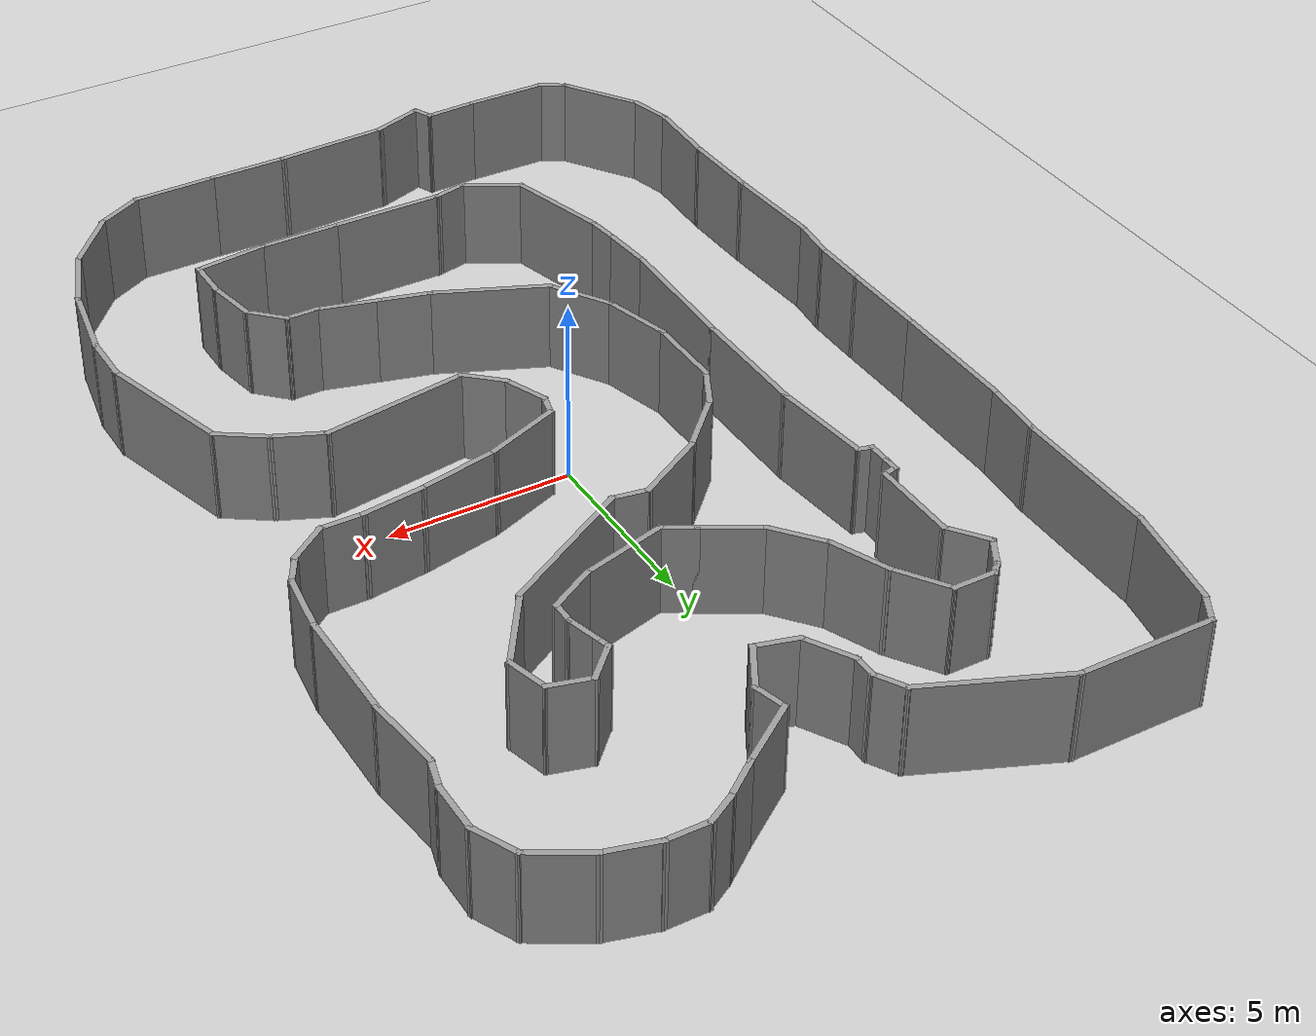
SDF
<sdf version="1.4">
 <world name="default">
  <light name="sun" type="directional">
   <pose>0 0 10 0 -0 0</pose>
   <diffuse>0.8 0.8 0.8 1</diffuse>
   <specular>0.2 0.2 0.2 1</specular>
   <attenuation>
    <range>1000</range>
    <constant>0.9</constant>
    <linear>0.01</linear>
    <quadratic>0.001</quadratic>
   </attenuation>
   <direction>-0.5 0.1 -0.9</direction>
  </light>
  <model name="ground_plane">
   <static>1</static>
   <link name="link">
    <collision name="collision">
     <geometry><plane><normal>0 0 1</normal><size>100 100</size></plane></geometry>
     <surface><friction><ode><mu>100</mu><mu2>50</mu2></ode></friction></surface>
    </collision>
    <visual name="visual">
     <cast_shadows>0</cast_shadows>
     <geometry><plane><normal>0 0 1</normal><size>100 100</size></plane></geometry>
     <material>
      <script><uri>file://media/materials/scripts/gazebo.material</uri><name>Gazebo/Grey</name></script>
     </material>
    </visual>
    <velocity_decay><linear>0</linear><angular>0</angular></velocity_decay>
   </link>
  </model>
  <physics type="ode">
   <max_step_size>0.001</max_step_size>
   <real_time_factor>1</real_time_factor>
   <real_time_update_rate>1000</real_time_update_rate>
   <gravity>0 0 -9.8</gravity>
  </physics>
  <scene><ambient>0.4 0.4 0.4 1</ambient><background>0.7 0.7 0.7 1</background><shadows>1</shadows></scene>
  <spherical_coordinates>
   <surface_model>EARTH_WGS84</surface_model>
   <latitude_deg>0</latitude_deg>
   <longitude_deg>0</longitude_deg>
   <elevation>0</elevation>
   <heading_deg>0</heading_deg>
  </spherical_coordinates>
  <model name="BuildingDefaultName">
   <link name="Wall_0">
    <collision name="Wall_0_Collision">
     <geometry><box><size>1.75 0.15 2.5</size></box></geometry>
     <pose>0 0 1.25 0 -0 0</pose>
    </collision>
    <visual name="Wall_0_Visual">
     <pose>0 0 1.25 0 -0 0</pose>
     <geometry><box><size>1.75 0.15 2.5</size></box></geometry>
     <material>
      <script><uri>file://media/materials/scripts/gazebo.material</uri><name>Gazebo/Grey</name></script>
     </material>
    </visual>
    <velocity_decay><linear>0</linear><angular>0</angular></velocity_decay>
    <pose>-9.13259 -1.69954 0 0 0 -1.5708</pose>
   </link>
   <link name="Wall_1">
    <collision name="Wall_1_Collision">
     <geometry><box><size>1.32231 0.15 2.5</size></box></geometry>
     <pose>0 0 1.25 0 -0 0</pose>
    </collision>
    <visual name="Wall_1_Visual">
     <pose>0 0 1.25 0 -0 0</pose>
     <geometry><box><size>1.32231 0.15 2.5</size></box></geometry>
     <material>
      <script><uri>file://media/materials/scripts/gazebo.material</uri><name>Gazebo/Grey</name></script>
     </material>
    </visual>
    <velocity_decay><linear>0</linear><angular>0</angular></velocity_decay>
    <pose>-9.19833 -3.082 0 0 0 -1.68319</pose>
   </link>
   <link name="Wall_2">
    <collision name="Wall_2_Collision">
     <geometry><box><size>0.673963 0.15 2.5</size></box></geometry>
     <pose>0 0 1.25 0 -0 0</pose>
    </collision>
    <visual name="Wall_2_Visual">
     <pose>0 0 1.25 0 -0 0</pose>
     <geometry><box><size>0.673963 0.15 2.5</size></box></geometry>
     <material>
      <script><uri>file://media/materials/scripts/gazebo.material</uri><name>Gazebo/Grey</name></script>
     </material>
    </visual>
    <velocity_decay><linear>0</linear><angular>0</angular></velocity_decay>
    <pose>-3.24793 -14.2675 0 0 0 -1.15257</pose>
   </link>
   <link name="Wall_3">
    <collision name="Wall_3_Collision">
     <geometry><box><size>2.06108 0.15 2.5</size></box></geometry>
     <pose>0 0 1.25 0 -0 0</pose>
    </collision>
    <visual name="Wall_3_Visual">
     <pose>0 0 1.25 0 -0 0</pose>
     <geometry><box><size>2.06108 0.15 2.5</size></box></geometry>
     <material>
      <script><uri>file://media/materials/scripts/gazebo.material</uri><name>Gazebo/Grey</name></script>
     </material>
    </visual>
    <velocity_decay><linear>0</linear><angular>0</angular></velocity_decay>
    <pose>4.6394 -9.86659 0 0 0 -3.0322</pose>
   </link>
   <link name="Wall_4">
    <collision name="Wall_4_Collision">
     <geometry><box><size>2.25 0.15 2.5</size></box></geometry>
     <pose>0 0 1.25 0 -0 0</pose>
    </collision>
    <visual name="Wall_4_Visual">
     <pose>0 0 1.25 0 -0 0</pose>
     <geometry><box><size>2.25 0.15 2.5</size></box></geometry>
     <material>
      <script><uri>file://media/materials/scripts/gazebo.material</uri><name>Gazebo/Grey</name></script>
     </material>
    </visual>
    <velocity_decay><linear>0</linear><angular>0</angular></velocity_decay>
    <pose>2.63957 -9.97091 0 0 -0 3.14159</pose>
   </link>
   <link name="Wall_5">
    <collision name="Wall_5_Collision">
     <geometry><box><size>3.25 0.15 2.5</size></box></geometry>
     <pose>0 0 1.25 0 -0 0</pose>
    </collision>
    <visual name="Wall_5_Visual">
     <pose>0 0 1.25 0 -0 0</pose>
     <geometry><box><size>3.25 0.15 2.5</size></box></geometry>
     <material>
      <script><uri>file://media/materials/scripts/gazebo.material</uri><name>Gazebo/Grey</name></script>
     </material>
    </visual>
    <velocity_decay><linear>0</linear><angular>0</angular></velocity_decay>
    <pose>0.039574 -9.97091 0 0 -0 3.14159</pose>
   </link>
   <link name="Wall_6">
    <collision name="Wall_6_Collision">
     <geometry><box><size>1.04919 0.15 2.5</size></box></geometry>
     <pose>0 0 1.25 0 -0 0</pose>
    </collision>
    <visual name="Wall_6_Visual">
     <pose>0 0 1.25 0 -0 0</pose>
     <geometry><box><size>1.04919 0.15 2.5</size></box></geometry>
     <material>
      <script><uri>file://media/materials/scripts/gazebo.material</uri><name>Gazebo/Grey</name></script>
     </material>
    </visual>
    <velocity_decay><linear>0</linear><angular>0</angular></velocity_decay>
    <pose>-1.94987 -10.0659 0 0 0 -2.92873</pose>
   </link>
   <link name="Wall_7">
    <collision name="Wall_7_Collision">
     <geometry><box><size>1.75 0.15 2.5</size></box></geometry>
     <pose>0 0 1.25 0 -0 0</pose>
    </collision>
    <visual name="Wall_7_Visual">
     <pose>0 0 1.25 0 -0 0</pose>
     <geometry><box><size>1.75 0.15 2.5</size></box></geometry>
     <material>
      <script><uri>file://media/materials/scripts/gazebo.material</uri><name>Gazebo/Grey</name></script>
     </material>
    </visual>
    <velocity_decay><linear>0</linear><angular>0</angular></velocity_decay>
    <pose>-3.08214 -9.76088 0 0 -0 2.61799</pose>
   </link>
   <link name="Wall_8">
    <collision name="Wall_8_Collision">
     <geometry><box><size>3 0.15 2.5</size></box></geometry>
     <pose>0 0 1.25 0 -0 0</pose>
    </collision>
    <visual name="Wall_8_Visual">
     <pose>0 0 1.25 0 -0 0</pose>
     <geometry><box><size>3 0.15 2.5</size></box></geometry>
     <material>
      <script><uri>file://media/materials/scripts/gazebo.material</uri><name>Gazebo/Grey</name></script>
     </material>
    </visual>
    <velocity_decay><linear>0</linear><angular>0</angular></velocity_decay>
    <pose>-4.14377 -7.98443 0 0 -0 1.8326</pose>
   </link>
   <link name="Wall_9">
    <collision name="Wall_9_Collision">
     <geometry><box><size>0.971593 0.15 2.5</size></box></geometry>
     <pose>0 0 1.25 0 -0 0</pose>
    </collision>
    <visual name="Wall_9_Visual">
     <pose>0 0 1.25 0 -0 0</pose>
     <geometry><box><size>0.971593 0.15 2.5</size></box></geometry>
     <material>
      <script><uri>file://media/materials/scripts/gazebo.material</uri><name>Gazebo/Grey</name></script>
     </material>
    </visual>
    <velocity_decay><linear>0</linear><angular>0</angular></velocity_decay>
    <pose>-4.55908 -6.19983 0 0 -0 1.68422</pose>
   </link>
   <link name="Wall_10">
    <collision name="Wall_10_Collision">
     <geometry><box><size>1.52602 0.15 2.5</size></box></geometry>
     <pose>0 0 1.25 0 -0 0</pose>
    </collision>
    <visual name="Wall_10_Visual">
     <pose>0 0 1.25 0 -0 0</pose>
     <geometry><box><size>1.52602 0.15 2.5</size></box></geometry>
     <material>
      <script><uri>file://media/materials/scripts/gazebo.material</uri><name>Gazebo/Grey</name></script>
     </material>
    </visual>
    <velocity_decay><linear>0</linear><angular>0</angular></velocity_decay>
    <pose>-4.65835 -5.10569 0 0 -0 1.64757</pose>
   </link>
   <link name="Wall_11">
    <collision name="Wall_11_Collision">
     <geometry><box><size>3.80308 0.15 2.5</size></box></geometry>
     <pose>0 0 1.25 0 -0 0</pose>
    </collision>
    <visual name="Wall_11_Visual">
     <pose>0 0 1.25 0 -0 0</pose>
     <geometry><box><size>3.80308 0.15 2.5</size></box></geometry>
     <material>
      <script><uri>file://media/materials/scripts/gazebo.material</uri><name>Gazebo/Grey</name></script>
     </material>
    </visual>
    <velocity_decay><linear>0</linear><angular>0</angular></velocity_decay>
    <pose>-4.65835 -2.59393 0 0 -0 1.5419</pose>
   </link>
   <link name="Wall_12">
    <collision name="Wall_12_Collision">
     <geometry><box><size>1.61374 0.15 2.5</size></box></geometry>
     <pose>0 0 1.25 0 -0 0</pose>
    </collision>
    <visual name="Wall_12_Visual">
     <pose>0 0 1.25 0 -0 0</pose>
     <geometry><box><size>1.61374 0.15 2.5</size></box></geometry>
     <material>
      <script><uri>file://media/materials/scripts/gazebo.material</uri><name>Gazebo/Grey</name></script>
     </material>
    </visual>
    <velocity_decay><linear>0</linear><angular>0</angular></velocity_decay>
    <pose>-2.44992 -14.2675 0 0 -0 0.333244</pose>
   </link>
   <link name="Wall_13">
    <collision name="Wall_13_Collision">
     <geometry><box><size>3.21191 0.15 2.5</size></box></geometry>
     <pose>0 0 1.25 0 -0 0</pose>
    </collision>
    <visual name="Wall_13_Visual">
     <pose>0 0 1.25 0 -0 0</pose>
     <geometry><box><size>3.21191 0.15 2.5</size></box></geometry>
     <material>
      <script><uri>file://media/materials/scripts/gazebo.material</uri><name>Gazebo/Grey</name></script>
     </material>
    </visual>
    <velocity_decay><linear>0</linear><angular>0</angular></velocity_decay>
    <pose>-0.228806 -13.9616 0 0 -0 0.043451</pose>
   </link>
   <link name="Wall_14">
    <collision name="Wall_14_Collision">
     <geometry><box><size>2.25158 0.15 2.5</size></box></geometry>
     <pose>0 0 1.25 0 -0 0</pose>
    </collision>
    <visual name="Wall_14_Visual">
     <pose>0 0 1.25 0 -0 0</pose>
     <geometry><box><size>2.25158 0.15 2.5</size></box></geometry>
     <material>
      <script><uri>file://media/materials/scripts/gazebo.material</uri><name>Gazebo/Grey</name></script>
     </material>
    </visual>
    <velocity_decay><linear>0</linear><angular>0</angular></velocity_decay>
    <pose>2.35141 -13.8951 0 0 -0 0</pose>
   </link>
   <link name="Wall_15">
    <collision name="Wall_15_Collision">
     <geometry><box><size>2.41117 0.15 2.5</size></box></geometry>
     <pose>0 0 1.25 0 -0 0</pose>
    </collision>
    <visual name="Wall_15_Visual">
     <pose>0 0 1.25 0 -0 0</pose>
     <geometry><box><size>2.41117 0.15 2.5</size></box></geometry>
     <material>
      <script><uri>file://media/materials/scripts/gazebo.material</uri><name>Gazebo/Grey</name></script>
     </material>
    </visual>
    <velocity_decay><linear>0</linear><angular>0</angular></velocity_decay>
    <pose>4.53263 -13.8818 0 0 -0 0.011764</pose>
   </link>
   <link name="Wall_16">
    <collision name="Wall_16_Collision">
     <geometry><box><size>1.53014 0.15 2.5</size></box></geometry>
     <pose>0 0 1.25 0 -0 0</pose>
    </collision>
    <visual name="Wall_16_Visual">
     <pose>0 0 1.25 0 -0 0</pose>
     <geometry><box><size>1.53014 0.15 2.5</size></box></geometry>
     <material>
      <script><uri>file://media/materials/scripts/gazebo.material</uri><name>Gazebo/Grey</name></script>
     </material>
    </visual>
    <velocity_decay><linear>0</linear><angular>0</angular></velocity_decay>
    <pose>6.27494 -13.5493 0 0 -0 0.480887</pose>
   </link>
   <link name="Wall_17">
    <collision name="Wall_17_Collision">
     <geometry><box><size>2.05428 0.15 2.5</size></box></geometry>
     <pose>0 0 1.25 0 -0 0</pose>
    </collision>
    <visual name="Wall_17_Visual">
     <pose>0 0 1.25 0 -0 0</pose>
     <geometry><box><size>2.05428 0.15 2.5</size></box></geometry>
     <material>
      <script><uri>file://media/materials/scripts/gazebo.material</uri><name>Gazebo/Grey</name></script>
     </material>
    </visual>
    <velocity_decay><linear>0</linear><angular>0</angular></velocity_decay>
    <pose>7.51185 -12.5119 0 0 -0 0.854594</pose>
   </link>
   <link name="Wall_18">
    <collision name="Wall_18_Collision">
     <geometry><box><size>2.09618 0.15 2.5</size></box></geometry>
     <pose>0 0 1.25 0 -0 0</pose>
    </collision>
    <visual name="Wall_18_Visual">
     <pose>0 0 1.25 0 -0 0</pose>
     <geometry><box><size>2.09618 0.15 2.5</size></box></geometry>
     <material>
      <script><uri>file://media/materials/scripts/gazebo.material</uri><name>Gazebo/Grey</name></script>
     </material>
    </visual>
    <velocity_decay><linear>0</linear><angular>0</angular></velocity_decay>
    <pose>8.49606 -10.8893 0 0 -0 1.19283</pose>
   </link>
   <link name="Wall_19">
    <collision name="Wall_19_Collision">
     <geometry><box><size>2.41976 0.15 2.5</size></box></geometry>
     <pose>0 0 1.25 0 -0 0</pose>
    </collision>
    <visual name="Wall_19_Visual">
     <pose>0 0 1.25 0 -0 0</pose>
     <geometry><box><size>2.41976 0.15 2.5</size></box></geometry>
     <material>
      <script><uri>file://media/materials/scripts/gazebo.material</uri><name>Gazebo/Grey</name></script>
     </material>
    </visual>
    <velocity_decay><linear>0</linear><angular>0</angular></velocity_decay>
    <pose>9.05466 -8.86771 0 0 -0 1.39409</pose>
   </link>
   <link name="Wall_20">
    <collision name="Wall_20_Collision">
     <geometry><box><size>1.5 0.15 2.5</size></box></geometry>
     <pose>0 0 1.25 0 -0 0</pose>
    </collision>
    <visual name="Wall_20_Visual">
     <pose>0 0 1.25 0 -0 0</pose>
     <geometry><box><size>1.5 0.15 2.5</size></box></geometry>
     <material>
      <script><uri>file://media/materials/scripts/gazebo.material</uri><name>Gazebo/Grey</name></script>
     </material>
    </visual>
    <velocity_decay><linear>0</linear><angular>0</angular></velocity_decay>
    <pose>9.25417 -7.0755 0 0 -0 1.5708</pose>
   </link>
   <link name="Wall_21">
    <collision name="Wall_21_Collision">
     <geometry><box><size>2.93747 0.15 2.5</size></box></geometry>
     <pose>0 0 1.25 0 -0 0</pose>
    </collision>
    <visual name="Wall_21_Visual">
     <pose>0 0 1.25 0 -0 0</pose>
     <geometry><box><size>2.93747 0.15 2.5</size></box></geometry>
     <material>
      <script><uri>file://media/materials/scripts/gazebo.material</uri><name>Gazebo/Grey</name></script>
     </material>
    </visual>
    <velocity_decay><linear>0</linear><angular>0</angular></velocity_decay>
    <pose>-9.18202 -5.05577 0 0 0 -1.51189</pose>
   </link>
   <link name="Wall_22">
    <collision name="Wall_22_Collision">
     <geometry><box><size>3.89422 0.15 2.5</size></box></geometry>
     <pose>0 0 1.25 0 -0 0</pose>
    </collision>
    <visual name="Wall_22_Visual">
     <pose>0 0 1.25 0 -0 0</pose>
     <geometry><box><size>3.89422 0.15 2.5</size></box></geometry>
     <material>
      <script><uri>file://media/materials/scripts/gazebo.material</uri><name>Gazebo/Grey</name></script>
     </material>
    </visual>
    <velocity_decay><linear>0</linear><angular>0</angular></velocity_decay>
    <pose>8.73546 -4.60168 0 0 -0 1.85154</pose>
   </link>
   <link name="Wall_23">
    <collision name="Wall_23_Collision">
     <geometry><box><size>1.52963 0.15 2.5</size></box></geometry>
     <pose>0 0 1.25 0 -0 0</pose>
    </collision>
    <visual name="Wall_23_Visual">
     <pose>0 0 1.25 0 -0 0</pose>
     <geometry><box><size>1.52963 0.15 2.5</size></box></geometry>
     <material>
      <script><uri>file://media/materials/scripts/gazebo.material</uri><name>Gazebo/Grey</name></script>
     </material>
    </visual>
    <velocity_decay><linear>0</linear><angular>0</angular></velocity_decay>
    <pose>7.64485 -2.41716 0 0 -0 2.54824</pose>
   </link>
   <link name="Wall_24">
    <collision name="Wall_24_Collision">
     <geometry><box><size>1.54366 0.15 2.5</size></box></geometry>
     <pose>0 0 1.25 0 -0 0</pose>
    </collision>
    <visual name="Wall_24_Visual">
     <pose>0 0 1.25 0 -0 0</pose>
     <geometry><box><size>1.54366 0.15 2.5</size></box></geometry>
     <material>
      <script><uri>file://media/materials/scripts/gazebo.material</uri><name>Gazebo/Grey</name></script>
     </material>
    </visual>
    <velocity_decay><linear>0</linear><angular>0</angular></velocity_decay>
    <pose>6.43454 -1.75215 0 0 -0 2.72918</pose>
   </link>
   <link name="Wall_25">
    <collision name="Wall_25_Collision">
     <geometry><box><size>4.10378 0.15 2.5</size></box></geometry>
     <pose>0 0 1.25 0 -0 0</pose>
    </collision>
    <visual name="Wall_25_Visual">
     <pose>0 0 1.25 0 -0 0</pose>
     <geometry><box><size>4.10378 0.15 2.5</size></box></geometry>
     <material>
      <script><uri>file://media/materials/scripts/gazebo.material</uri><name>Gazebo/Grey</name></script>
     </material>
    </visual>
    <velocity_decay><linear>0</linear><angular>0</angular></velocity_decay>
    <pose>3.84102 -1.76545 0 0 0 -2.99303</pose>
   </link>
   <link name="Wall_26">
    <collision name="Wall_26_Collision">
     <geometry><box><size>1.29875 0.15 2.5</size></box></geometry>
     <pose>0 0 1.25 0 -0 0</pose>
    </collision>
    <visual name="Wall_26_Visual">
     <pose>0 0 1.25 0 -0 0</pose>
     <geometry><box><size>1.29875 0.15 2.5</size></box></geometry>
     <material>
      <script><uri>file://media/materials/scripts/gazebo.material</uri><name>Gazebo/Grey</name></script>
     </material>
    </visual>
    <velocity_decay><linear>0</linear><angular>0</angular></velocity_decay>
    <pose>1.46031 -1.67235 0 0 -0 2.40534</pose>
   </link>
   <link name="Wall_27">
    <collision name="Wall_27_Collision">
     <geometry><box><size>1.35526 0.15 2.5</size></box></geometry>
     <pose>0 0 1.25 0 -0 0</pose>
    </collision>
    <visual name="Wall_27_Visual">
     <pose>0 0 1.25 0 -0 0</pose>
     <geometry><box><size>1.35526 0.15 2.5</size></box></geometry>
     <material>
      <script><uri>file://media/materials/scripts/gazebo.material</uri><name>Gazebo/Grey</name></script>
     </material>
    </visual>
    <velocity_decay><linear>0</linear><angular>0</angular></velocity_decay>
    <pose>0.808602 -0.728047 0 0 -0 1.9554</pose>
   </link>
   <link name="Wall_28">
    <collision name="Wall_28_Collision">
     <geometry><box><size>0.75 0.15 2.5</size></box></geometry>
     <pose>0 0 1.25 0 -0 0</pose>
    </collision>
    <visual name="Wall_28_Visual">
     <pose>0 0 1.25 0 -0 0</pose>
     <geometry><box><size>0.75 0.15 2.5</size></box></geometry>
     <material>
      <script><uri>file://media/materials/scripts/gazebo.material</uri><name>Gazebo/Grey</name></script>
     </material>
    </visual>
    <velocity_decay><linear>0</linear><angular>0</angular></velocity_decay>
    <pose>0.660146 0.120334 0 0 -0 1.309</pose>
   </link>
   <link name="Wall_29">
    <collision name="Wall_29_Collision">
     <geometry><box><size>2.23581 0.15 2.5</size></box></geometry>
     <pose>0 0 1.25 0 -0 0</pose>
    </collision>
    <visual name="Wall_29_Visual">
     <pose>0 0 1.25 0 -0 0</pose>
     <geometry><box><size>2.23581 0.15 2.5</size></box></geometry>
     <material>
      <script><uri>file://media/materials/scripts/gazebo.material</uri><name>Gazebo/Grey</name></script>
     </material>
    </visual>
    <velocity_decay><linear>0</linear><angular>0</angular></velocity_decay>
    <pose>1.71085 0.785339 0 0 -0 0.368044</pose>
   </link>
   <link name="Wall_30">
    <collision name="Wall_30_Collision">
     <geometry><box><size>2.35156 0.15 2.5</size></box></geometry>
     <pose>0 0 1.25 0 -0 0</pose>
    </collision>
    <visual name="Wall_30_Visual">
     <pose>0 0 1.25 0 -0 0</pose>
     <geometry><box><size>2.35156 0.15 2.5</size></box></geometry>
     <material>
      <script><uri>file://media/materials/scripts/gazebo.material</uri><name>Gazebo/Grey</name></script>
     </material>
    </visual>
    <velocity_decay><linear>0</linear><angular>0</angular></velocity_decay>
    <pose>3.76122 1.38667 0 0 -0 0.206874</pose>
   </link>
   <link name="Wall_31">
    <collision name="Wall_31_Collision">
     <geometry><box><size>1.78651 0.15 2.5</size></box></geometry>
     <pose>0 0 1.25 0 -0 0</pose>
    </collision>
    <visual name="Wall_31_Visual">
     <pose>0 0 1.25 0 -0 0</pose>
     <geometry><box><size>1.78651 0.15 2.5</size></box></geometry>
     <material>
      <script><uri>file://media/materials/scripts/gazebo.material</uri><name>Gazebo/Grey</name></script>
     </material>
    </visual>
    <velocity_decay><linear>0</linear><angular>0</angular></velocity_decay>
    <pose>5.64984 1.71917 0 0 -0 0.130403</pose>
   </link>
   <link name="Wall_32">
    <collision name="Wall_32_Collision">
     <geometry><box><size>2.30527 0.15 2.5</size></box></geometry>
     <pose>0 0 1.25 0 -0 0</pose>
    </collision>
    <visual name="Wall_32_Visual">
     <pose>0 0 1.25 0 -0 0</pose>
     <geometry><box><size>2.30527 0.15 2.5</size></box></geometry>
     <material>
      <script><uri>file://media/materials/scripts/gazebo.material</uri><name>Gazebo/Grey</name></script>
     </material>
    </visual>
    <velocity_decay><linear>0</linear><angular>0</angular></velocity_decay>
    <pose>-9.07337 -7.5244 0 0 0 -1.54611</pose>
   </link>
   <link name="Wall_33">
    <collision name="Wall_33_Collision">
     <geometry><box><size>1.25 0.15 2.5</size></box></geometry>
     <pose>0 0 1.25 0 -0 0</pose>
    </collision>
    <visual name="Wall_33_Visual">
     <pose>0 0 1.25 0 -0 0</pose>
     <geometry><box><size>1.25 0.15 2.5</size></box></geometry>
     <material>
      <script><uri>file://media/materials/scripts/gazebo.material</uri><name>Gazebo/Grey</name></script>
     </material>
    </visual>
    <velocity_decay><linear>0</linear><angular>0</angular></velocity_decay>
    <pose>7.01114 1.82557 0 0 -0 0</pose>
   </link>
   <link name="Wall_34">
    <collision name="Wall_34_Collision">
     <geometry><box><size>1.32364 0.15 2.5</size></box></geometry>
     <pose>0 0 1.25 0 -0 0</pose>
    </collision>
    <visual name="Wall_34_Visual">
     <pose>0 0 1.25 0 -0 0</pose>
     <geometry><box><size>1.32364 0.15 2.5</size></box></geometry>
     <material>
      <script><uri>file://media/materials/scripts/gazebo.material</uri><name>Gazebo/Grey</name></script>
     </material>
    </visual>
    <velocity_decay><linear>0</linear><angular>0</angular></velocity_decay>
    <pose>8.03525 2.17137 0 0 -0 0.63017</pose>
   </link>
   <link name="Wall_35">
    <collision name="Wall_35_Collision">
     <geometry><box><size>1 0.15 2.5</size></box></geometry>
     <pose>0 0 1.25 0 -0 0</pose>
    </collision>
    <visual name="Wall_35_Visual">
     <pose>0 0 1.25 0 -0 0</pose>
     <geometry><box><size>1 0.15 2.5</size></box></geometry>
     <material>
      <script><uri>file://media/materials/scripts/gazebo.material</uri><name>Gazebo/Grey</name></script>
     </material>
    </visual>
    <velocity_decay><linear>0</linear><angular>0</angular></velocity_decay>
    <pose>8.72186 2.88524 0 0 -0 1.0472</pose>
   </link>
   <link name="Wall_36">
    <collision name="Wall_36_Collision">
     <geometry><box><size>1.7952 0.15 2.5</size></box></geometry>
     <pose>0 0 1.25 0 -0 0</pose>
    </collision>
    <visual name="Wall_36_Visual">
     <pose>0 0 1.25 0 -0 0</pose>
     <geometry><box><size>1.7952 0.15 2.5</size></box></geometry>
     <material>
      <script><uri>file://media/materials/scripts/gazebo.material</uri><name>Gazebo/Grey</name></script>
     </material>
    </visual>
    <velocity_decay><linear>0</linear><angular>0</angular></velocity_decay>
    <pose>9.04106 4.06895 0 0 -0 1.44072</pose>
   </link>
   <link name="Wall_37">
    <collision name="Wall_37_Collision">
     <geometry><box><size>3.25 0.15 2.5</size></box></geometry>
     <pose>0 0 1.25 0 -0 0</pose>
    </collision>
    <visual name="Wall_37_Visual">
     <pose>0 0 1.25 0 -0 0</pose>
     <geometry><box><size>3.25 0.15 2.5</size></box></geometry>
     <material>
      <script><uri>file://media/materials/scripts/gazebo.material</uri><name>Gazebo/Grey</name></script>
     </material>
    </visual>
    <velocity_decay><linear>0</linear><angular>0</angular></velocity_decay>
    <pose>9.14776 6.43459 0 0 -0 1.5708</pose>
   </link>
   <link name="Wall_38">
    <collision name="Wall_38_Collision">
     <geometry><box><size>2.19788 0.15 2.5</size></box></geometry>
     <pose>0 0 1.25 0 -0 0</pose>
    </collision>
    <visual name="Wall_38_Visual">
     <pose>0 0 1.25 0 -0 0</pose>
     <geometry><box><size>2.19788 0.15 2.5</size></box></geometry>
     <material>
      <script><uri>file://media/materials/scripts/gazebo.material</uri><name>Gazebo/Grey</name></script>
     </material>
    </visual>
    <velocity_decay><linear>0</linear><angular>0</angular></velocity_decay>
    <pose>9.02806 9.00151 0 0 -0 1.68797</pose>
   </link>
   <link name="Wall_39">
    <collision name="Wall_39_Collision">
     <geometry><box><size>1 0.15 2.5</size></box></geometry>
     <pose>0 0 1.25 0 -0 0</pose>
    </collision>
    <visual name="Wall_39_Visual">
     <pose>0 0 1.25 0 -0 0</pose>
     <geometry><box><size>1 0.15 2.5</size></box></geometry>
     <material>
      <script><uri>file://media/materials/scripts/gazebo.material</uri><name>Gazebo/Grey</name></script>
     </material>
    </visual>
    <velocity_decay><linear>0</linear><angular>0</angular></velocity_decay>
    <pose>9.01836 10.429 0 0 -0 1.309</pose>
   </link>
   <link name="Wall_40">
    <collision name="Wall_40_Collision">
     <geometry><box><size>1.5 0.15 2.5</size></box></geometry>
     <pose>0 0 1.25 0 -0 0</pose>
    </collision>
    <visual name="Wall_40_Visual">
     <pose>0 0 1.25 0 -0 0</pose>
     <geometry><box><size>1.5 0.15 2.5</size></box></geometry>
     <material>
      <script><uri>file://media/materials/scripts/gazebo.material</uri><name>Gazebo/Grey</name></script>
     </material>
    </visual>
    <velocity_decay><linear>0</linear><angular>0</angular></velocity_decay>
    <pose>9.12836 11.5145 0 0 -0 1.5708</pose>
   </link>
   <link name="Wall_41">
    <collision name="Wall_41_Collision">
     <geometry><box><size>1.36429 0.15 2.5</size></box></geometry>
     <pose>0 0 1.25 0 -0 0</pose>
    </collision>
    <visual name="Wall_41_Visual">
     <pose>0 0 1.25 0 -0 0</pose>
     <geometry><box><size>1.36429 0.15 2.5</size></box></geometry>
     <material>
      <script><uri>file://media/materials/scripts/gazebo.material</uri><name>Gazebo/Grey</name></script>
     </material>
    </visual>
    <velocity_decay><linear>0</linear><angular>0</angular></velocity_decay>
    <pose>8.87206 12.7399 0 0 -0 2.0066</pose>
   </link>
   <link name="Wall_42">
    <collision name="Wall_42_Collision">
     <geometry><box><size>1.75 0.15 2.5</size></box></geometry>
     <pose>0 0 1.25 0 -0 0</pose>
    </collision>
    <visual name="Wall_42_Visual">
     <pose>0 0 1.25 0 -0 0</pose>
     <geometry><box><size>1.75 0.15 2.5</size></box></geometry>
     <material>
      <script><uri>file://media/materials/scripts/gazebo.material</uri><name>Gazebo/Grey</name></script>
     </material>
    </visual>
    <velocity_decay><linear>0</linear><angular>0</angular></velocity_decay>
    <pose>7.92294 13.6903 0 0 -0 2.61799</pose>
   </link>
   <link name="Wall_43">
    <collision name="Wall_43_Collision">
     <geometry><box><size>2.19977 0.15 2.5</size></box></geometry>
     <pose>0 0 1.25 0 -0 0</pose>
    </collision>
    <visual name="Wall_43_Visual">
     <pose>0 0 1.25 0 -0 0</pose>
     <geometry><box><size>2.19977 0.15 2.5</size></box></geometry>
     <material>
      <script><uri>file://media/materials/scripts/gazebo.material</uri><name>Gazebo/Grey</name></script>
     </material>
    </visual>
    <velocity_decay><linear>0</linear><angular>0</angular></velocity_decay>
    <pose>-9.08667 -9.62581 0 0 0 -1.60974</pose>
   </link>
   <link name="Wall_44">
    <collision name="Wall_44_Collision">
     <geometry><box><size>1.5 0.15 2.5</size></box></geometry>
     <pose>0 0 1.25 0 -0 0</pose>
    </collision>
    <visual name="Wall_44_Visual">
     <pose>0 0 1.25 0 -0 0</pose>
     <geometry><box><size>1.5 0.15 2.5</size></box></geometry>
     <material>
      <script><uri>file://media/materials/scripts/gazebo.material</uri><name>Gazebo/Grey</name></script>
     </material>
    </visual>
    <velocity_decay><linear>0</linear><angular>0</angular></velocity_decay>
    <pose>6.57812 14.265 0 0 -0 2.87979</pose>
   </link>
   <link name="Wall_45">
    <collision name="Wall_45_Collision">
     <geometry><box><size>1.25 0.15 2.5</size></box></geometry>
     <pose>0 0 1.25 0 -0 0</pose>
    </collision>
    <visual name="Wall_45_Visual">
     <pose>0 0 1.25 0 -0 0</pose>
     <geometry><box><size>1.25 0.15 2.5</size></box></geometry>
     <material>
      <script><uri>file://media/materials/scripts/gazebo.material</uri><name>Gazebo/Grey</name></script>
     </material>
    </visual>
    <velocity_decay><linear>0</linear><angular>0</angular></velocity_decay>
    <pose>5.37612 14.4397 0 0 -0 3.14159</pose>
   </link>
   <link name="Wall_46">
    <collision name="Wall_46_Collision">
     <geometry><box><size>1 0.15 2.5</size></box></geometry>
     <pose>0 0 1.25 0 -0 0</pose>
    </collision>
    <visual name="Wall_46_Visual">
     <pose>0 0 1.25 0 -0 0</pose>
     <geometry><box><size>1 0.15 2.5</size></box></geometry>
     <material>
      <script><uri>file://media/materials/scripts/gazebo.material</uri><name>Gazebo/Grey</name></script>
     </material>
    </visual>
    <velocity_decay><linear>0</linear><angular>0</angular></velocity_decay>
    <pose>4.45806 14.2272 0 0 0 -2.61799</pose>
   </link>
   <link name="Wall_47">
    <collision name="Wall_47_Collision">
     <geometry><box><size>1.28671 0.15 2.5</size></box></geometry>
     <pose>0 0 1.25 0 -0 0</pose>
    </collision>
    <visual name="Wall_47_Visual">
     <pose>0 0 1.25 0 -0 0</pose>
     <geometry><box><size>1.28671 0.15 2.5</size></box></geometry>
     <material>
      <script><uri>file://media/materials/scripts/gazebo.material</uri><name>Gazebo/Grey</name></script>
     </material>
    </visual>
    <velocity_decay><linear>0</linear><angular>0</angular></velocity_decay>
    <pose>3.63675 13.6717 0 0 0 -2.4939</pose>
   </link>
   <link name="Wall_48">
    <collision name="Wall_48_Collision">
     <geometry><box><size>2.03405 0.15 2.5</size></box></geometry>
     <pose>0 0 1.25 0 -0 0</pose>
    </collision>
    <visual name="Wall_48_Visual">
     <pose>0 0 1.25 0 -0 0</pose>
     <geometry><box><size>2.03405 0.15 2.5</size></box></geometry>
     <material>
      <script><uri>file://media/materials/scripts/gazebo.material</uri><name>Gazebo/Grey</name></script>
     </material>
    </visual>
    <velocity_decay><linear>0</linear><angular>0</angular></velocity_decay>
    <pose>2.41262 12.7874 0 0 0 -2.52927</pose>
   </link>
   <link name="Wall_49">
    <collision name="Wall_49_Collision">
     <geometry><box><size>1 0.15 2.5</size></box></geometry>
     <pose>0 0 1.25 0 -0 0</pose>
    </collision>
    <visual name="Wall_49_Visual">
     <pose>0 0 1.25 0 -0 0</pose>
     <geometry><box><size>1 0.15 2.5</size></box></geometry>
     <material>
      <script><uri>file://media/materials/scripts/gazebo.material</uri><name>Gazebo/Grey</name></script>
     </material>
    </visual>
    <velocity_decay><linear>0</linear><angular>0</angular></velocity_decay>
    <pose>1.75175 11.8354 0 0 0 -1.309</pose>
   </link>
   <link name="Wall_50">
    <collision name="Wall_50_Collision">
     <geometry><box><size>1.5 0.15 2.5</size></box></geometry>
     <pose>0 0 1.25 0 -0 0</pose>
    </collision>
    <visual name="Wall_50_Visual">
     <pose>0 0 1.25 0 -0 0</pose>
     <geometry><box><size>1.5 0.15 2.5</size></box></geometry>
     <material>
      <script><uri>file://media/materials/scripts/gazebo.material</uri><name>Gazebo/Grey</name></script>
     </material>
    </visual>
    <velocity_decay><linear>0</linear><angular>0</angular></velocity_decay>
    <pose>1.52425 10.8403 0 0 0 -2.0944</pose>
   </link>
   <link name="Wall_51">
    <collision name="Wall_51_Collision">
     <geometry><box><size>1.25 0.15 2.5</size></box></geometry>
     <pose>0 0 1.25 0 -0 0</pose>
    </collision>
    <visual name="Wall_51_Visual">
     <pose>0 0 1.25 0 -0 0</pose>
     <geometry><box><size>1.25 0.15 2.5</size></box></geometry>
     <material>
      <script><uri>file://media/materials/scripts/gazebo.material</uri><name>Gazebo/Grey</name></script>
     </material>
    </visual>
    <velocity_decay><linear>0</linear><angular>0</angular></velocity_decay>
    <pose>0.655486 10.3981 0 0 -0 2.87979</pose>
   </link>
   <link name="Wall_52">
    <collision name="Wall_52_Collision">
     <geometry><box><size>1.5 0.15 2.5</size></box></geometry>
     <pose>0 0 1.25 0 -0 0</pose>
    </collision>
    <visual name="Wall_52_Visual">
     <pose>0 0 1.25 0 -0 0</pose>
     <geometry><box><size>1.5 0.15 2.5</size></box></geometry>
     <material>
      <script><uri>file://media/materials/scripts/gazebo.material</uri><name>Gazebo/Grey</name></script>
     </material>
    </visual>
    <velocity_decay><linear>0</linear><angular>0</angular></velocity_decay>
    <pose>-0.213273 11.125 0 0 -0 2.0944</pose>
   </link>
   <link name="Wall_53">
    <collision name="Wall_53_Collision">
     <geometry><box><size>0.75 0.15 2.5</size></box></geometry>
     <pose>0 0 1.25 0 -0 0</pose>
    </collision>
    <visual name="Wall_53_Visual">
     <pose>0 0 1.25 0 -0 0</pose>
     <geometry><box><size>0.75 0.15 2.5</size></box></geometry>
     <material>
      <script><uri>file://media/materials/scripts/gazebo.material</uri><name>Gazebo/Grey</name></script>
     </material>
    </visual>
    <velocity_decay><linear>0</linear><angular>0</angular></velocity_decay>
    <pose>-0.550773 12.0096 0 0 -0 1.5708</pose>
   </link>
   <link name="Wall_54">
    <collision name="Wall_54_Collision">
     <geometry><box><size>1.29844 0.15 2.5</size></box></geometry>
     <pose>0 0 1.25 0 -0 0</pose>
    </collision>
    <visual name="Wall_54_Visual">
     <pose>0 0 1.25 0 -0 0</pose>
     <geometry><box><size>1.29844 0.15 2.5</size></box></geometry>
     <material>
      <script><uri>file://media/materials/scripts/gazebo.material</uri><name>Gazebo/Grey</name></script>
     </material>
    </visual>
    <velocity_decay><linear>0</linear><angular>0</angular></velocity_decay>
    <pose>-8.99357 -11.2085 0 0 0 -1.33705</pose>
   </link>
   <link name="Wall_55">
    <collision name="Wall_55_Collision">
     <geometry><box><size>1 0.15 2.5</size></box></geometry>
     <pose>0 0 1.25 0 -0 0</pose>
    </collision>
    <visual name="Wall_55_Visual">
     <pose>0 0 1.25 0 -0 0</pose>
     <geometry><box><size>1 0.15 2.5</size></box></geometry>
     <material>
      <script><uri>file://media/materials/scripts/gazebo.material</uri><name>Gazebo/Grey</name></script>
     </material>
    </visual>
    <velocity_decay><linear>0</linear><angular>0</angular></velocity_decay>
    <pose>-0.763273 12.6777 0 0 -0 2.0944</pose>
   </link>
   <link name="Wall_56">
    <collision name="Wall_56_Collision">
     <geometry><box><size>3.91935 0.15 2.5</size></box></geometry>
     <pose>0 0 1.25 0 -0 0</pose>
    </collision>
    <visual name="Wall_56_Visual">
     <pose>0 0 1.25 0 -0 0</pose>
     <geometry><box><size>3.91935 0.15 2.5</size></box></geometry>
     <material>
      <script><uri>file://media/materials/scripts/gazebo.material</uri><name>Gazebo/Grey</name></script>
     </material>
    </visual>
    <velocity_decay><linear>0</linear><angular>0</angular></velocity_decay>
    <pose>-2.7138 13.7746 0 0 -0 2.7445</pose>
   </link>
   <link name="Wall_57">
    <collision name="Wall_57_Collision">
     <geometry><box><size>3.75 0.15 2.5</size></box></geometry>
     <pose>0 0 1.25 0 -0 0</pose>
    </collision>
    <visual name="Wall_57_Visual">
     <pose>0 0 1.25 0 -0 0</pose>
     <geometry><box><size>3.75 0.15 2.5</size></box></geometry>
     <material>
      <script><uri>file://media/materials/scripts/gazebo.material</uri><name>Gazebo/Grey</name></script>
     </material>
    </visual>
    <velocity_decay><linear>0</linear><angular>0</angular></velocity_decay>
    <pose>-6.25183 14.5035 0 0 -0 3.14159</pose>
   </link>
   <link name="Wall_58">
    <collision name="Wall_58_Collision">
     <geometry><box><size>1 0.15 2.5</size></box></geometry>
     <pose>0 0 1.25 0 -0 0</pose>
    </collision>
    <visual name="Wall_58_Visual">
     <pose>0 0 1.25 0 -0 0</pose>
     <geometry><box><size>1 0.15 2.5</size></box></geometry>
     <material>
      <script><uri>file://media/materials/scripts/gazebo.material</uri><name>Gazebo/Grey</name></script>
     </material>
    </visual>
    <velocity_decay><linear>0</linear><angular>0</angular></velocity_decay>
    <pose>-8.26432 14.1354 0 0 0 -2.0944</pose>
   </link>
   <link name="Wall_59">
    <collision name="Wall_59_Collision">
     <geometry><box><size>3.13491 0.15 2.5</size></box></geometry>
     <pose>0 0 1.25 0 -0 0</pose>
    </collision>
    <visual name="Wall_59_Visual">
     <pose>0 0 1.25 0 -0 0</pose>
     <geometry><box><size>3.13491 0.15 2.5</size></box></geometry>
     <material>
      <script><uri>file://media/materials/scripts/gazebo.material</uri><name>Gazebo/Grey</name></script>
     </material>
    </visual>
    <velocity_decay><linear>0</linear><angular>0</angular></velocity_decay>
    <pose>-8.74941 12.3 0 0 0 -1.75447</pose>
   </link>
   <link name="Wall_60">
    <collision name="Wall_60_Collision">
     <geometry><box><size>4.25 0.15 2.5</size></box></geometry>
     <pose>0 0 1.25 0 -0 0</pose>
    </collision>
    <visual name="Wall_60_Visual">
     <pose>0 0 1.25 0 -0 0</pose>
     <geometry><box><size>4.25 0.15 2.5</size></box></geometry>
     <material>
      <script><uri>file://media/materials/scripts/gazebo.material</uri><name>Gazebo/Grey</name></script>
     </material>
    </visual>
    <velocity_decay><linear>0</linear><angular>0</angular></velocity_decay>
    <pose>-9.02201 8.78267 0 0 0 -1.5708</pose>
   </link>
   <link name="Wall_61">
    <collision name="Wall_61_Collision">
     <geometry><box><size>1.85231 0.15 2.5</size></box></geometry>
     <pose>0 0 1.25 0 -0 0</pose>
    </collision>
    <visual name="Wall_61_Visual">
     <pose>0 0 1.25 0 -0 0</pose>
     <geometry><box><size>1.85231 0.15 2.5</size></box></geometry>
     <material>
      <script><uri>file://media/materials/scripts/gazebo.material</uri><name>Gazebo/Grey</name></script>
     </material>
    </visual>
    <velocity_decay><linear>0</linear><angular>0</angular></velocity_decay>
    <pose>-9.09337 5.88451 0 0 0 -1.65475</pose>
   </link>
   <link name="Wall_62">
    <collision name="Wall_62_Collision">
     <geometry><box><size>3.75 0.15 2.5</size></box></geometry>
     <pose>0 0 1.25 0 -0 0</pose>
    </collision>
    <visual name="Wall_62_Visual">
     <pose>0 0 1.25 0 -0 0</pose>
     <geometry><box><size>3.75 0.15 2.5</size></box></geometry>
     <material>
      <script><uri>file://media/materials/scripts/gazebo.material</uri><name>Gazebo/Grey</name></script>
     </material>
    </visual>
    <velocity_decay><linear>0</linear><angular>0</angular></velocity_decay>
    <pose>-9.16474 3.23635 0 0 0 -1.5708</pose>
   </link>
   <link name="Wall_63">
    <collision name="Wall_63_Collision">
     <geometry><box><size>2.48611 0.15 2.5</size></box></geometry>
     <pose>0 0 1.25 0 -0 0</pose>
    </collision>
    <visual name="Wall_63_Visual">
     <pose>0 0 1.25 0 -0 0</pose>
     <geometry><box><size>2.48611 0.15 2.5</size></box></geometry>
     <material>
      <script><uri>file://media/materials/scripts/gazebo.material</uri><name>Gazebo/Grey</name></script>
     </material>
    </visual>
    <velocity_decay><linear>0</linear><angular>0</angular></velocity_decay>
    <pose>-9.14867 0.268403 0 0 0 -1.55703</pose>
   </link>
   <link name="Wall_64">
    <collision name="Wall_64_Collision">
     <geometry><box><size>2.4518 0.15 2.5</size></box></geometry>
     <pose>0 0 1.25 0 -0 0</pose>
    </collision>
    <visual name="Wall_64_Visual">
     <pose>0 0 1.25 0 -0 0</pose>
     <geometry><box><size>2.4518 0.15 2.5</size></box></geometry>
     <material>
      <script><uri>file://media/materials/scripts/gazebo.material</uri><name>Gazebo/Grey</name></script>
     </material>
    </visual>
    <velocity_decay><linear>0</linear><angular>0</angular></velocity_decay>
    <pose>-8.22217 -12.7247 0 0 0 -0.982794</pose>
   </link>
   <link name="Wall_65">
    <collision name="Wall_65_Collision">
     <geometry><box><size>3.5 0.15 2.5</size></box></geometry>
     <pose>0 0 1.25 0 -0 0</pose>
    </collision>
    <visual name="Wall_65_Visual">
     <pose>0 0 1.25 0 -0 0</pose>
     <geometry><box><size>3.5 0.15 2.5</size></box></geometry>
     <material>
      <script><uri>file://media/materials/scripts/gazebo.material</uri><name>Gazebo/Grey</name></script>
     </material>
    </visual>
    <velocity_decay><linear>0</linear><angular>0</angular></velocity_decay>
    <pose>-4.60558 0.970175 0 0 -0 1.5708</pose>
   </link>
   <link name="Wall_66">
    <collision name="Wall_66_Collision">
     <geometry><box><size>2.91365 0.15 2.5</size></box></geometry>
     <pose>0 0 1.25 0 -0 0</pose>
    </collision>
    <visual name="Wall_66_Visual">
     <pose>0 0 1.25 0 -0 0</pose>
     <geometry><box><size>2.91365 0.15 2.5</size></box></geometry>
     <material>
      <script><uri>file://media/materials/scripts/gazebo.material</uri><name>Gazebo/Grey</name></script>
     </material>
    </visual>
    <velocity_decay><linear>0</linear><angular>0</angular></velocity_decay>
    <pose>-4.74277 4.02017 0 0 -0 1.67025</pose>
   </link>
   <link name="Wall_67">
    <collision name="Wall_67_Collision">
     <geometry><box><size>0.5 0.15 2.5</size></box></geometry>
     <pose>0 0 1.25 0 -0 0</pose>
    </collision>
    <visual name="Wall_67_Visual">
     <pose>0 0 1.25 0 -0 0</pose>
     <geometry><box><size>0.5 0.15 2.5</size></box></geometry>
     <material>
      <script><uri>file://media/materials/scripts/gazebo.material</uri><name>Gazebo/Grey</name></script>
     </material>
    </visual>
    <velocity_decay><linear>0</linear><angular>0</angular></velocity_decay>
    <pose>-5.04901 5.44047 0 0 -0 2.87979</pose>
   </link>
   <link name="Wall_68">
    <collision name="Wall_68_Collision">
     <geometry><box><size>0.75 0.15 2.5</size></box></geometry>
     <pose>0 0 1.25 0 -0 0</pose>
    </collision>
    <visual name="Wall_68_Visual">
     <pose>0 0 1.25 0 -0 0</pose>
     <geometry><box><size>0.75 0.15 2.5</size></box></geometry>
     <material>
      <script><uri>file://media/materials/scripts/gazebo.material</uri><name>Gazebo/Grey</name></script>
     </material>
    </visual>
    <velocity_decay><linear>0</linear><angular>0</angular></velocity_decay>
    <pose>-5.21805 5.78576 0 0 -0 1.5708</pose>
   </link>
   <link name="Wall_69">
    <collision name="Wall_69_Collision">
     <geometry><box><size>0.5 0.15 2.5</size></box></geometry>
     <pose>0 0 1.25 0 -0 0</pose>
    </collision>
    <visual name="Wall_69_Visual">
     <pose>0 0 1.25 0 -0 0</pose>
     <geometry><box><size>0.5 0.15 2.5</size></box></geometry>
     <material>
      <script><uri>file://media/materials/scripts/gazebo.material</uri><name>Gazebo/Grey</name></script>
     </material>
    </visual>
    <velocity_decay><linear>0</linear><angular>0</angular></velocity_decay>
    <pose>-5.21805 6.26076 0 0 -0 1.5708</pose>
   </link>
   <link name="Wall_70">
    <collision name="Wall_70_Collision">
     <geometry><box><size>0.5 0.15 2.5</size></box></geometry>
     <pose>0 0 1.25 0 -0 0</pose>
    </collision>
    <visual name="Wall_70_Visual">
     <pose>0 0 1.25 0 -0 0</pose>
     <geometry><box><size>0.5 0.15 2.5</size></box></geometry>
     <material>
      <script><uri>file://media/materials/scripts/gazebo.material</uri><name>Gazebo/Grey</name></script>
     </material>
    </visual>
    <velocity_decay><linear>0</linear><angular>0</angular></velocity_decay>
    <pose>-5.04901 6.48105 0 0 -0 0.261799</pose>
   </link>
   <link name="Wall_71">
    <collision name="Wall_71_Collision">
     <geometry><box><size>2.5 0.15 2.5</size></box></geometry>
     <pose>0 0 1.25 0 -0 0</pose>
    </collision>
    <visual name="Wall_71_Visual">
     <pose>0 0 1.25 0 -0 0</pose>
     <geometry><box><size>2.5 0.15 2.5</size></box></geometry>
     <material>
      <script><uri>file://media/materials/scripts/gazebo.material</uri><name>Gazebo/Grey</name></script>
     </material>
    </visual>
    <velocity_decay><linear>0</linear><angular>0</angular></velocity_decay>
    <pose>-4.87997 7.70135 0 0 -0 1.5708</pose>
   </link>
   <link name="Wall_72">
    <collision name="Wall_72_Collision">
     <geometry><box><size>1.31212 0.15 2.5</size></box></geometry>
     <pose>0 0 1.25 0 -0 0</pose>
    </collision>
    <visual name="Wall_72_Visual">
     <pose>0 0 1.25 0 -0 0</pose>
     <geometry><box><size>1.31212 0.15 2.5</size></box></geometry>
     <material>
      <script><uri>file://media/materials/scripts/gazebo.material</uri><name>Gazebo/Grey</name></script>
     </material>
    </visual>
    <velocity_decay><linear>0</linear><angular>0</angular></velocity_decay>
    <pose>-5.22824 9.34147 0 0 -0 2.21351</pose>
   </link>
   <link name="Wall_73">
    <collision name="Wall_73_Collision">
     <geometry><box><size>1 0.15 2.5</size></box></geometry>
     <pose>0 0 1.25 0 -0 0</pose>
    </collision>
    <visual name="Wall_73_Visual">
     <pose>0 0 1.25 0 -0 0</pose>
     <geometry><box><size>1 0.15 2.5</size></box></geometry>
     <material>
      <script><uri>file://media/materials/scripts/gazebo.material</uri><name>Gazebo/Grey</name></script>
     </material>
    </visual>
    <velocity_decay><linear>0</linear><angular>0</angular></velocity_decay>
    <pose>-5.36401 10.1746 0 0 -0 1.0472</pose>
   </link>
   <link name="Wall_74">
    <collision name="Wall_74_Collision">
     <geometry><box><size>0.5 0.15 2.5</size></box></geometry>
     <pose>0 0 1.25 0 -0 0</pose>
    </collision>
    <visual name="Wall_74_Visual">
     <pose>0 0 1.25 0 -0 0</pose>
     <geometry><box><size>0.5 0.15 2.5</size></box></geometry>
     <material>
      <script><uri>file://media/materials/scripts/gazebo.material</uri><name>Gazebo/Grey</name></script>
     </material>
    </visual>
    <velocity_decay><linear>0</linear><angular>0</angular></velocity_decay>
    <pose>-5.02777 10.6665 0 0 -0 0.785398</pose>
   </link>
   <link name="Wall_75">
    <collision name="Wall_75_Collision">
     <geometry><box><size>0.866232 0.15 2.5</size></box></geometry>
     <pose>0 0 1.25 0 -0 0</pose>
    </collision>
    <visual name="Wall_75_Visual">
     <pose>0 0 1.25 0 -0 0</pose>
     <geometry><box><size>0.866232 0.15 2.5</size></box></geometry>
     <material>
      <script><uri>file://media/materials/scripts/gazebo.material</uri><name>Gazebo/Grey</name></script>
     </material>
    </visual>
    <velocity_decay><linear>0</linear><angular>0</angular></velocity_decay>
    <pose>-7.27786 -13.8685 0 0 0 -0.546789</pose>
   </link>
   <link name="Wall_76">
    <collision name="Wall_76_Collision">
     <geometry><box><size>1.25 0.15 2.5</size></box></geometry>
     <pose>0 0 1.25 0 -0 0</pose>
    </collision>
    <visual name="Wall_76_Visual">
     <pose>0 0 1.25 0 -0 0</pose>
     <geometry><box><size>1.25 0.15 2.5</size></box></geometry>
     <material>
      <script><uri>file://media/materials/scripts/gazebo.material</uri><name>Gazebo/Grey</name></script>
     </material>
    </visual>
    <velocity_decay><linear>0</linear><angular>0</angular></velocity_decay>
    <pose>-4.35402 10.7902 0 0 -0 0</pose>
   </link>
   <link name="Wall_77">
    <collision name="Wall_77_Collision">
     <geometry><box><size>1.69465 0.15 2.5</size></box></geometry>
     <pose>0 0 1.25 0 -0 0</pose>
    </collision>
    <visual name="Wall_77_Visual">
     <pose>0 0 1.25 0 -0 0</pose>
     <geometry><box><size>1.69465 0.15 2.5</size></box></geometry>
     <material>
      <script><uri>file://media/materials/scripts/gazebo.material</uri><name>Gazebo/Grey</name></script>
     </material>
    </visual>
    <velocity_decay><linear>0</linear><angular>0</angular></velocity_decay>
    <pose>-3.37106 10.1506 0 0 0 -0.975694</pose>
   </link>
   <link name="Wall_78">
    <collision name="Wall_78_Collision">
     <geometry><box><size>1.75748 0.15 2.5</size></box></geometry>
     <pose>0 0 1.25 0 -0 0</pose>
    </collision>
    <visual name="Wall_78_Visual">
     <pose>0 0 1.25 0 -0 0</pose>
     <geometry><box><size>1.75748 0.15 2.5</size></box></geometry>
     <material>
      <script><uri>file://media/materials/scripts/gazebo.material</uri><name>Gazebo/Grey</name></script>
     </material>
    </visual>
    <velocity_decay><linear>0</linear><angular>0</angular></velocity_decay>
    <pose>-2.6215 8.77233 0 0 0 -1.1659</pose>
   </link>
   <link name="Wall_79">
    <collision name="Wall_79_Collision">
     <geometry><box><size>1.64995 0.15 2.5</size></box></geometry>
     <pose>0 0 1.25 0 -0 0</pose>
    </collision>
    <visual name="Wall_79_Visual">
     <pose>0 0 1.25 0 -0 0</pose>
     <geometry><box><size>1.64995 0.15 2.5</size></box></geometry>
     <material>
      <script><uri>file://media/materials/scripts/gazebo.material</uri><name>Gazebo/Grey</name></script>
     </material>
    </visual>
    <velocity_decay><linear>0</linear><angular>0</angular></velocity_decay>
    <pose>-1.82997 7.45313 0 0 0 -0.885067</pose>
   </link>
   <link name="Wall_80">
    <collision name="Wall_80_Collision">
     <geometry><box><size>1.75 0.15 2.5</size></box></geometry>
     <pose>0 0 1.25 0 -0 0</pose>
    </collision>
    <visual name="Wall_80_Visual">
     <pose>0 0 1.25 0 -0 0</pose>
     <geometry><box><size>1.75 0.15 2.5</size></box></geometry>
     <material>
      <script><uri>file://media/materials/scripts/gazebo.material</uri><name>Gazebo/Grey</name></script>
     </material>
    </visual>
    <velocity_decay><linear>0</linear><angular>0</angular></velocity_decay>
    <pose>-0.66224 6.47268 0 0 0 -0.523599</pose>
   </link>
   <link name="Wall_81">
    <collision name="Wall_81_Collision">
     <geometry><box><size>1 0.15 2.5</size></box></geometry>
     <pose>0 0 1.25 0 -0 0</pose>
    </collision>
    <visual name="Wall_81_Visual">
     <pose>0 0 1.25 0 -0 0</pose>
     <geometry><box><size>1 0.15 2.5</size></box></geometry>
     <material>
      <script><uri>file://media/materials/scripts/gazebo.material</uri><name>Gazebo/Grey</name></script>
     </material>
    </visual>
    <velocity_decay><linear>0</linear><angular>0</angular></velocity_decay>
    <pose>0.398641 5.86018 0 0 0 -0.523599</pose>
   </link>
   <link name="Wall_82">
    <collision name="Wall_82_Collision">
     <geometry><box><size>2.5 0.15 2.5</size></box></geometry>
     <pose>0 0 1.25 0 -0 0</pose>
    </collision>
    <visual name="Wall_82_Visual">
     <pose>0 0 1.25 0 -0 0</pose>
     <geometry><box><size>2.5 0.15 2.5</size></box></geometry>
     <material>
      <script><uri>file://media/materials/scripts/gazebo.material</uri><name>Gazebo/Grey</name></script>
     </material>
    </visual>
    <velocity_decay><linear>0</linear><angular>0</angular></velocity_decay>
    <pose>1.90166 5.95179 0 0 -0 0.261799</pose>
   </link>
   <link name="Wall_83">
    <collision name="Wall_83_Collision">
     <geometry><box><size>1.5 0.15 2.5</size></box></geometry>
     <pose>0 0 1.25 0 -0 0</pose>
    </collision>
    <visual name="Wall_83_Visual">
     <pose>0 0 1.25 0 -0 0</pose>
     <geometry><box><size>1.5 0.15 2.5</size></box></geometry>
     <material>
      <script><uri>file://media/materials/scripts/gazebo.material</uri><name>Gazebo/Grey</name></script>
     </material>
    </visual>
    <velocity_decay><linear>0</linear><angular>0</angular></velocity_decay>
    <pose>3.6212 6.5934 0 0 -0 0.523599</pose>
   </link>
   <link name="Wall_84">
    <collision name="Wall_84_Collision">
     <geometry><box><size>0.75 0.15 2.5</size></box></geometry>
     <pose>0 0 1.25 0 -0 0</pose>
    </collision>
    <visual name="Wall_84_Visual">
     <pose>0 0 1.25 0 -0 0</pose>
     <geometry><box><size>0.75 0.15 2.5</size></box></geometry>
     <material>
      <script><uri>file://media/materials/scripts/gazebo.material</uri><name>Gazebo/Grey</name></script>
     </material>
    </visual>
    <velocity_decay><linear>0</linear><angular>0</angular></velocity_decay>
    <pose>4.20576 7.23091 0 0 -0 1.5708</pose>
   </link>
   <link name="Wall_85">
    <collision name="Wall_85_Collision">
     <geometry><box><size>1 0.15 2.5</size></box></geometry>
     <pose>0 0 1.25 0 -0 0</pose>
    </collision>
    <visual name="Wall_85_Visual">
     <pose>0 0 1.25 0 -0 0</pose>
     <geometry><box><size>1 0.15 2.5</size></box></geometry>
     <material>
      <script><uri>file://media/materials/scripts/gazebo.material</uri><name>Gazebo/Grey</name></script>
     </material>
    </visual>
    <velocity_decay><linear>0</linear><angular>0</angular></velocity_decay>
    <pose>4.09576 7.94142 0 0 -0 1.8326</pose>
   </link>
   <link name="Wall_86">
    <collision name="Wall_86_Collision">
     <geometry><box><size>2.38457 0.15 2.5</size></box></geometry>
     <pose>0 0 1.25 0 -0 0</pose>
    </collision>
    <visual name="Wall_86_Visual">
     <pose>0 0 1.25 0 -0 0</pose>
     <geometry><box><size>2.38457 0.15 2.5</size></box></geometry>
     <material>
      <script><uri>file://media/materials/scripts/gazebo.material</uri><name>Gazebo/Grey</name></script>
     </material>
    </visual>
    <velocity_decay><linear>0</linear><angular>0</angular></velocity_decay>
    <pose>-5.85475 -14.068 0 0 0 -0.011904</pose>
   </link>
   <link name="Wall_87">
    <collision name="Wall_87_Collision">
     <geometry><box><size>0.5 0.15 2.5</size></box></geometry>
     <pose>0 0 1.25 0 -0 0</pose>
    </collision>
    <visual name="Wall_87_Visual">
     <pose>0 0 1.25 0 -0 0</pose>
     <geometry><box><size>0.5 0.15 2.5</size></box></geometry>
     <material>
      <script><uri>file://media/materials/scripts/gazebo.material</uri><name>Gazebo/Grey</name></script>
     </material>
    </visual>
    <velocity_decay><linear>0</linear><angular>0</angular></velocity_decay>
    <pose>3.94047 8.52098 0 0 -0 1.8326</pose>
   </link>
   <link name="Wall_88">
    <collision name="Wall_88_Collision">
     <geometry><box><size>1.25 0.15 2.5</size></box></geometry>
     <pose>0 0 1.25 0 -0 0</pose>
    </collision>
    <visual name="Wall_88_Visual">
     <pose>0 0 1.25 0 -0 0</pose>
     <geometry><box><size>1.25 0.15 2.5</size></box></geometry>
     <material>
      <script><uri>file://media/materials/scripts/gazebo.material</uri><name>Gazebo/Grey</name></script>
     </material>
    </visual>
    <velocity_decay><linear>0</linear><angular>0</angular></velocity_decay>
    <pose>4.28409 9.07892 0 0 -0 0.785398</pose>
   </link>
   <link name="Wall_89">
    <collision name="Wall_89_Collision">
     <geometry><box><size>1.25 0.15 2.5</size></box></geometry>
     <pose>0 0 1.25 0 -0 0</pose>
    </collision>
    <visual name="Wall_89_Visual">
     <pose>0 0 1.25 0 -0 0</pose>
     <geometry><box><size>1.25 0.15 2.5</size></box></geometry>
     <material>
      <script><uri>file://media/materials/scripts/gazebo.material</uri><name>Gazebo/Grey</name></script>
     </material>
    </visual>
    <velocity_decay><linear>0</linear><angular>0</angular></velocity_decay>
    <pose>5.20426 9.32548 0 0 0 -0.261799</pose>
   </link>
   <link name="Wall_90">
    <collision name="Wall_90_Collision">
     <geometry><box><size>1.25 0.15 2.5</size></box></geometry>
     <pose>0 0 1.25 0 -0 0</pose>
    </collision>
    <visual name="Wall_90_Visual">
     <pose>0 0 1.25 0 -0 0</pose>
     <geometry><box><size>1.25 0.15 2.5</size></box></geometry>
     <material>
      <script><uri>file://media/materials/scripts/gazebo.material</uri><name>Gazebo/Grey</name></script>
     </material>
    </visual>
    <velocity_decay><linear>0</linear><angular>0</angular></velocity_decay>
    <pose>5.87786 8.65187 0 0 0 -1.309</pose>
   </link>
   <link name="Wall_91">
    <collision name="Wall_91_Collision">
     <geometry><box><size>2.46947 0.15 2.5</size></box></geometry>
     <pose>0 0 1.25 0 -0 0</pose>
    </collision>
    <visual name="Wall_91_Visual">
     <pose>0 0 1.25 0 -0 0</pose>
     <geometry><box><size>2.46947 0.15 2.5</size></box></geometry>
     <material>
      <script><uri>file://media/materials/scripts/gazebo.material</uri><name>Gazebo/Grey</name></script>
     </material>
    </visual>
    <velocity_decay><linear>0</linear><angular>0</angular></velocity_decay>
    <pose>5.37202 7.15893 0 0 0 -2.16387</pose>
   </link>
   <link name="Wall_92">
    <collision name="Wall_92_Collision">
     <geometry><box><size>4.25 0.15 2.5</size></box></geometry>
     <pose>0 0 1.25 0 -0 0</pose>
    </collision>
    <visual name="Wall_92_Visual">
     <pose>0 0 1.25 0 -0 0</pose>
     <geometry><box><size>4.25 0.15 2.5</size></box></geometry>
     <material>
      <script><uri>file://media/materials/scripts/gazebo.material</uri><name>Gazebo/Grey</name></script>
     </material>
    </visual>
    <velocity_decay><linear>0</linear><angular>0</angular></velocity_decay>
    <pose>2.94848 5.17225 0 0 0 -2.61799</pose>
   </link>
   <link name="Wall_93">
    <collision name="Wall_93_Collision">
     <geometry><box><size>1.06536 0.15 2.5</size></box></geometry>
     <pose>0 0 1.25 0 -0 0</pose>
    </collision>
    <visual name="Wall_93_Visual">
     <pose>0 0 1.25 0 -0 0</pose>
     <geometry><box><size>1.06536 0.15 2.5</size></box></geometry>
     <material>
      <script><uri>file://media/materials/scripts/gazebo.material</uri><name>Gazebo/Grey</name></script>
     </material>
    </visual>
    <velocity_decay><linear>0</linear><angular>0</angular></velocity_decay>
    <pose>0.721662 4.22242 0 0 -0 2.9766</pose>
   </link>
   <link name="Wall_94">
    <collision name="Wall_94_Collision">
     <geometry><box><size>2.25 0.15 2.5</size></box></geometry>
     <pose>0 0 1.25 0 -0 0</pose>
    </collision>
    <visual name="Wall_94_Visual">
     <pose>0 0 1.25 0 -0 0</pose>
     <geometry><box><size>2.25 0.15 2.5</size></box></geometry>
     <material>
      <script><uri>file://media/materials/scripts/gazebo.material</uri><name>Gazebo/Grey</name></script>
     </material>
    </visual>
    <velocity_decay><linear>0</linear><angular>0</angular></velocity_decay>
    <pose>-0.639128 3.77259 0 0 0 -2.61799</pose>
   </link>
   <link name="Wall_95">
    <collision name="Wall_95_Collision">
     <geometry><box><size>2 0.15 2.5</size></box></geometry>
     <pose>0 0 1.25 0 -0 0</pose>
    </collision>
    <visual name="Wall_95_Visual">
     <pose>0 0 1.25 0 -0 0</pose>
     <geometry><box><size>2 0.15 2.5</size></box></geometry>
     <material>
      <script><uri>file://media/materials/scripts/gazebo.material</uri><name>Gazebo/Grey</name></script>
     </material>
    </visual>
    <velocity_decay><linear>0</linear><angular>0</angular></velocity_decay>
    <pose>-2.20253 2.59352 0 0 0 -2.35619</pose>
   </link>
   <link name="Wall_96">
    <collision name="Wall_96_Collision">
     <geometry><box><size>1.37184 0.15 2.5</size></box></geometry>
     <pose>0 0 1.25 0 -0 0</pose>
    </collision>
    <visual name="Wall_96_Visual">
     <pose>0 0 1.25 0 -0 0</pose>
     <geometry><box><size>1.37184 0.15 2.5</size></box></geometry>
     <material>
      <script><uri>file://media/materials/scripts/gazebo.material</uri><name>Gazebo/Grey</name></script>
     </material>
    </visual>
    <velocity_decay><linear>0</linear><angular>0</angular></velocity_decay>
    <pose>-3.14009 1.39828 0 0 0 -2.05333</pose>
   </link>
   <link name="Wall_97">
    <collision name="Wall_97_Collision">
     <geometry><box><size>1.53423 0.15 2.5</size></box></geometry>
     <pose>0 0 1.25 0 -0 0</pose>
    </collision>
    <visual name="Wall_97_Visual">
     <pose>0 0 1.25 0 -0 0</pose>
     <geometry><box><size>1.53423 0.15 2.5</size></box></geometry>
     <material>
      <script><uri>file://media/materials/scripts/gazebo.material</uri><name>Gazebo/Grey</name></script>
     </material>
    </visual>
    <velocity_decay><linear>0</linear><angular>0</angular></velocity_decay>
    <pose>-4.04594 -14.0547 0 0 -0 0.038443</pose>
   </link>
   <link name="Wall_98">
    <collision name="Wall_98_Collision">
     <geometry><box><size>2.25 0.15 2.5</size></box></geometry>
     <pose>0 0 1.25 0 -0 0</pose>
    </collision>
    <visual name="Wall_98_Visual">
     <pose>0 0 1.25 0 -0 0</pose>
     <geometry><box><size>2.25 0.15 2.5</size></box></geometry>
     <material>
      <script><uri>file://media/materials/scripts/gazebo.material</uri><name>Gazebo/Grey</name></script>
     </material>
    </visual>
    <velocity_decay><linear>0</linear><angular>0</angular></velocity_decay>
    <pose>-3.42357 -0.192888 0 0 0 -1.5708</pose>
   </link>
   <link name="Wall_99">
    <collision name="Wall_99_Collision">
     <geometry><box><size>2 0.15 2.5</size></box></geometry>
     <pose>0 0 1.25 0 -0 0</pose>
    </collision>
    <visual name="Wall_99_Visual">
     <pose>0 0 1.25 0 -0 0</pose>
     <geometry><box><size>2 0.15 2.5</size></box></geometry>
     <material>
      <script><uri>file://media/materials/scripts/gazebo.material</uri><name>Gazebo/Grey</name></script>
     </material>
    </visual>
    <velocity_decay><linear>0</linear><angular>0</angular></velocity_decay>
    <pose>-3.18416 -2.13637 0 0 0 -1.309</pose>
   </link>
   <link name="Wall_100">
    <collision name="Wall_100_Collision">
     <geometry><box><size>1.92512 0.15 2.5</size></box></geometry>
     <pose>0 0 1.25 0 -0 0</pose>
    </collision>
    <visual name="Wall_100_Visual">
     <pose>0 0 1.25 0 -0 0</pose>
     <geometry><box><size>1.92512 0.15 2.5</size></box></geometry>
     <material>
      <script><uri>file://media/materials/scripts/gazebo.material</uri><name>Gazebo/Grey</name></script>
     </material>
    </visual>
    <velocity_decay><linear>0</linear><angular>0</angular></velocity_decay>
    <pose>-2.46652 -3.77754 0 0 0 -1.00175</pose>
   </link>
   <link name="Wall_101">
    <collision name="Wall_101_Collision">
     <geometry><box><size>3.25133 0.15 2.5</size></box></geometry>
     <pose>0 0 1.25 0 -0 0</pose>
    </collision>
    <visual name="Wall_101_Visual">
     <pose>0 0 1.25 0 -0 0</pose>
     <geometry><box><size>3.25133 0.15 2.5</size></box></geometry>
     <material>
      <script><uri>file://media/materials/scripts/gazebo.material</uri><name>Gazebo/Grey</name></script>
     </material>
    </visual>
    <velocity_decay><linear>0</linear><angular>0</angular></velocity_decay>
    <pose>-0.563538 -5.13735 0 0 0 -0.405785</pose>
   </link>
   <link name="Wall_102">
    <collision name="Wall_102_Collision">
     <geometry><box><size>1.5 0.15 2.5</size></box></geometry>
     <pose>0 0 1.25 0 -0 0</pose>
    </collision>
    <visual name="Wall_102_Visual">
     <pose>0 0 1.25 0 -0 0</pose>
     <geometry><box><size>1.5 0.15 2.5</size></box></geometry>
     <material>
      <script><uri>file://media/materials/scripts/gazebo.material</uri><name>Gazebo/Grey</name></script>
     </material>
    </visual>
    <velocity_decay><linear>0</linear><angular>0</angular></velocity_decay>
    <pose>1.5132 -5.92416 0 0 0 -0.261799</pose>
   </link>
   <link name="Wall_103">
    <collision name="Wall_103_Collision">
     <geometry><box><size>1.75 0.15 2.5</size></box></geometry>
     <pose>0 0 1.25 0 -0 0</pose>
    </collision>
    <visual name="Wall_103_Visual">
     <pose>0 0 1.25 0 -0 0</pose>
     <geometry><box><size>1.75 0.15 2.5</size></box></geometry>
     <material>
      <script><uri>file://media/materials/scripts/gazebo.material</uri><name>Gazebo/Grey</name></script>
     </material>
    </visual>
    <velocity_decay><linear>0</linear><angular>0</angular></velocity_decay>
    <pose>2.93794 -6.30592 0 0 0 -0.261799</pose>
   </link>
   <link name="Wall_104">
    <collision name="Wall_104_Collision">
     <geometry><box><size>1 0.15 2.5</size></box></geometry>
     <pose>0 0 1.25 0 -0 0</pose>
    </collision>
    <visual name="Wall_104_Visual">
     <pose>0 0 1.25 0 -0 0</pose>
     <geometry><box><size>1 0.15 2.5</size></box></geometry>
     <material>
      <script><uri>file://media/materials/scripts/gazebo.material</uri><name>Gazebo/Grey</name></script>
     </material>
    </visual>
    <velocity_decay><linear>0</linear><angular>0</angular></velocity_decay>
    <pose>4.13568 -6.51298 0 0 -0 0</pose>
   </link>
   <link name="Wall_105">
    <collision name="Wall_105_Collision">
     <geometry><box><size>1.25 0.15 2.5</size></box></geometry>
     <pose>0 0 1.25 0 -0 0</pose>
    </collision>
    <visual name="Wall_105_Visual">
     <pose>0 0 1.25 0 -0 0</pose>
     <geometry><box><size>1.25 0.15 2.5</size></box></geometry>
     <material>
      <script><uri>file://media/materials/scripts/gazebo.material</uri><name>Gazebo/Grey</name></script>
     </material>
    </visual>
    <velocity_decay><linear>0</linear><angular>0</angular></velocity_decay>
    <pose>4.94959 -6.90189 0 0 0 -0.785398</pose>
   </link>
   <link name="Wall_106">
    <collision name="Wall_106_Collision">
     <geometry><box><size>1.5442 0.15 2.5</size></box></geometry>
     <pose>0 0 1.25 0 -0 0</pose>
    </collision>
    <visual name="Wall_106_Visual">
     <pose>0 0 1.25 0 -0 0</pose>
     <geometry><box><size>1.5442 0.15 2.5</size></box></geometry>
     <material>
      <script><uri>file://media/materials/scripts/gazebo.material</uri><name>Gazebo/Grey</name></script>
     </material>
    </visual>
    <velocity_decay><linear>0</linear><angular>0</angular></velocity_decay>
    <pose>5.46386 -7.97653 0 0 0 -1.38998</pose>
   </link>
   <link name="Wall_107">
    <collision name="Wall_107_Collision">
     <geometry><box><size>1.25 0.15 2.5</size></box></geometry>
     <pose>0 0 1.25 0 -0 0</pose>
    </collision>
    <visual name="Wall_107_Visual">
     <pose>0 0 1.25 0 -0 0</pose>
     <geometry><box><size>1.25 0.15 2.5</size></box></geometry>
     <material>
      <script><uri>file://media/materials/scripts/gazebo.material</uri><name>Gazebo/Grey</name></script>
     </material>
    </visual>
    <velocity_decay><linear>0</linear><angular>0</angular></velocity_decay>
    <pose>5.58923 -9.21226 0 0 0 -1.5708</pose>
   </link>
   <static>1</static>
  </model>
 </world>
</sdf>
